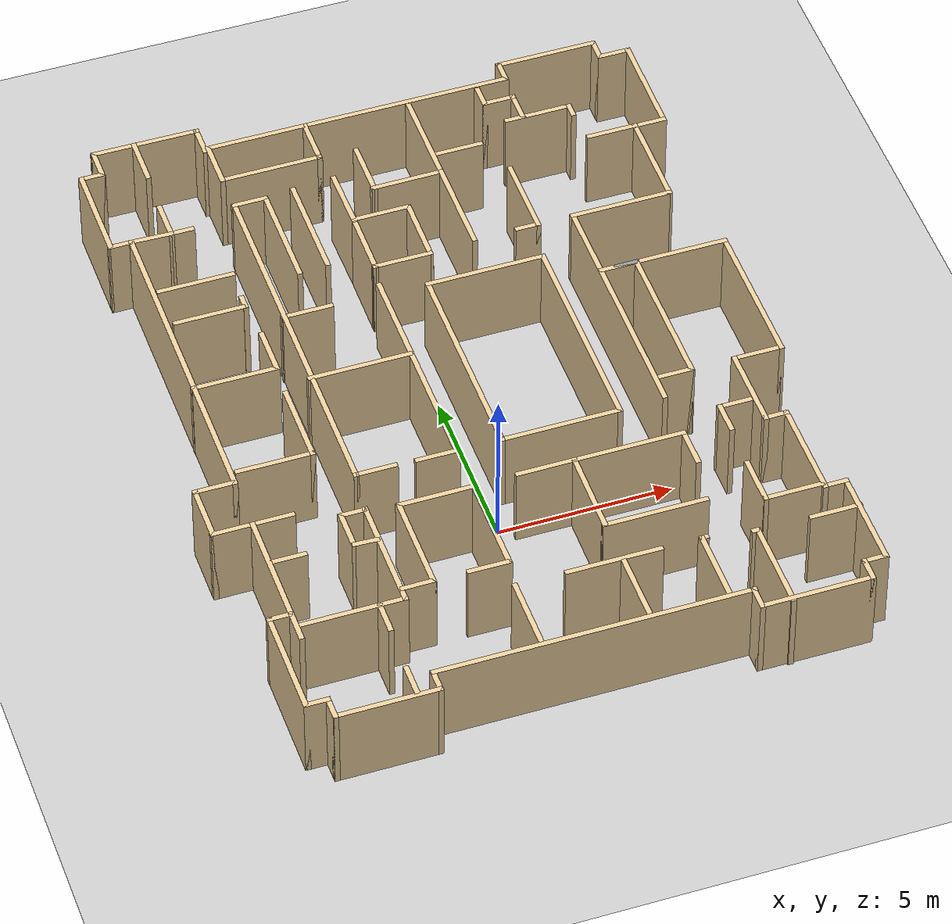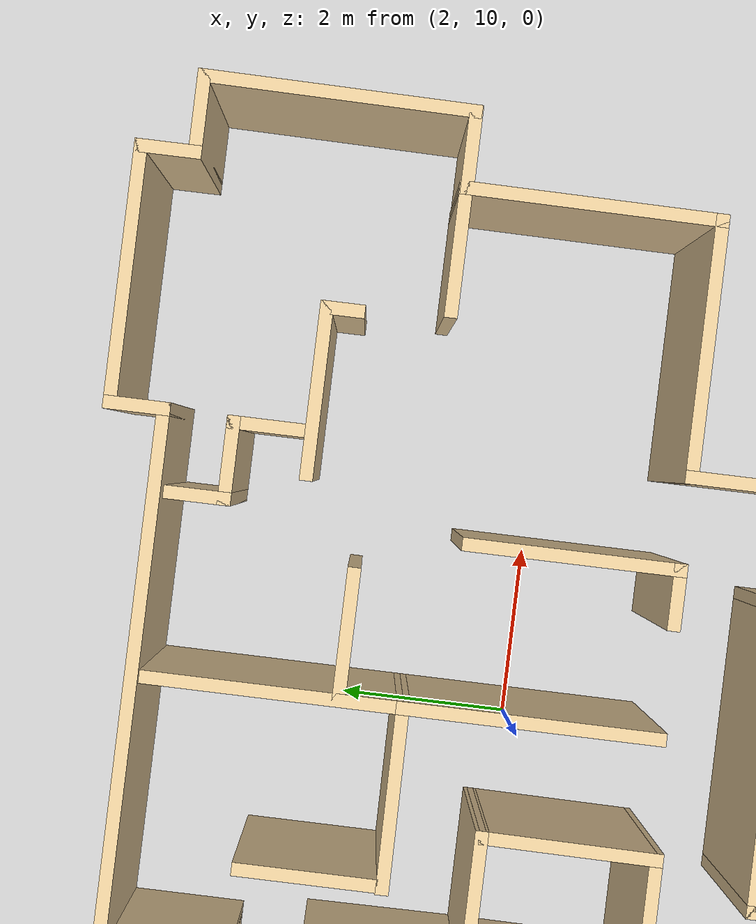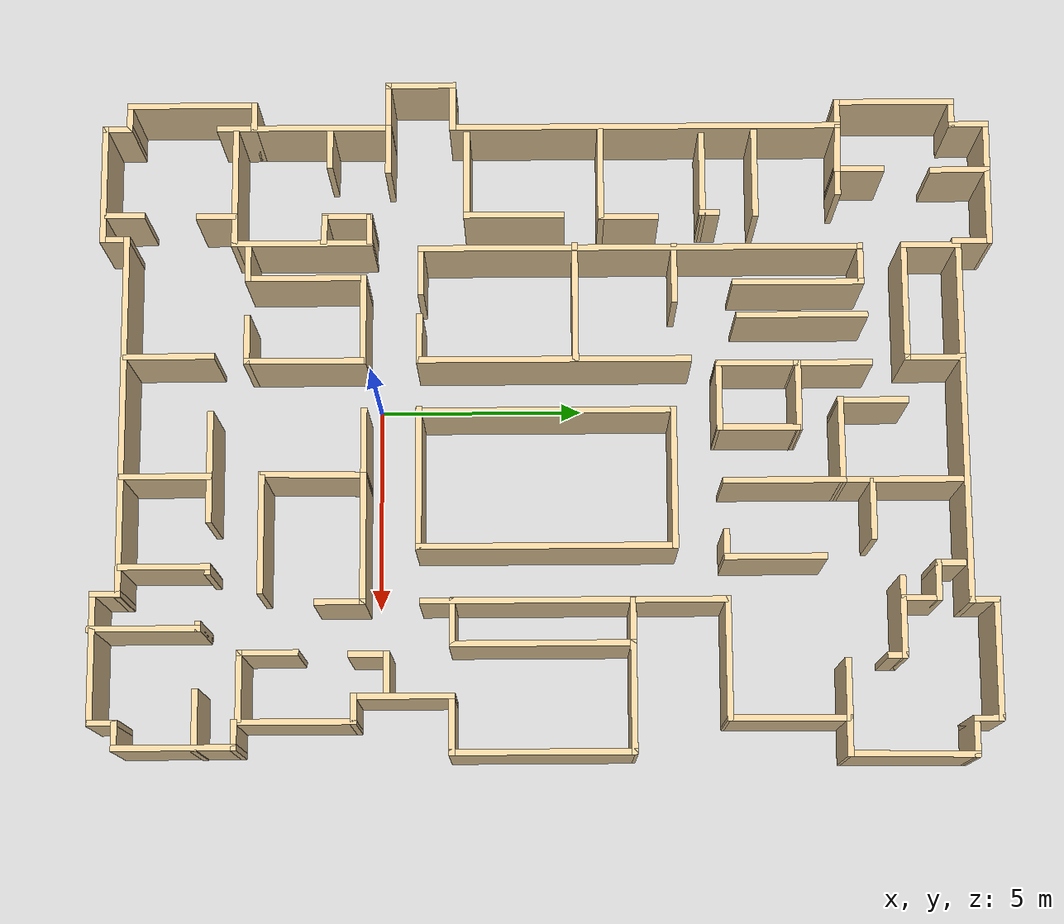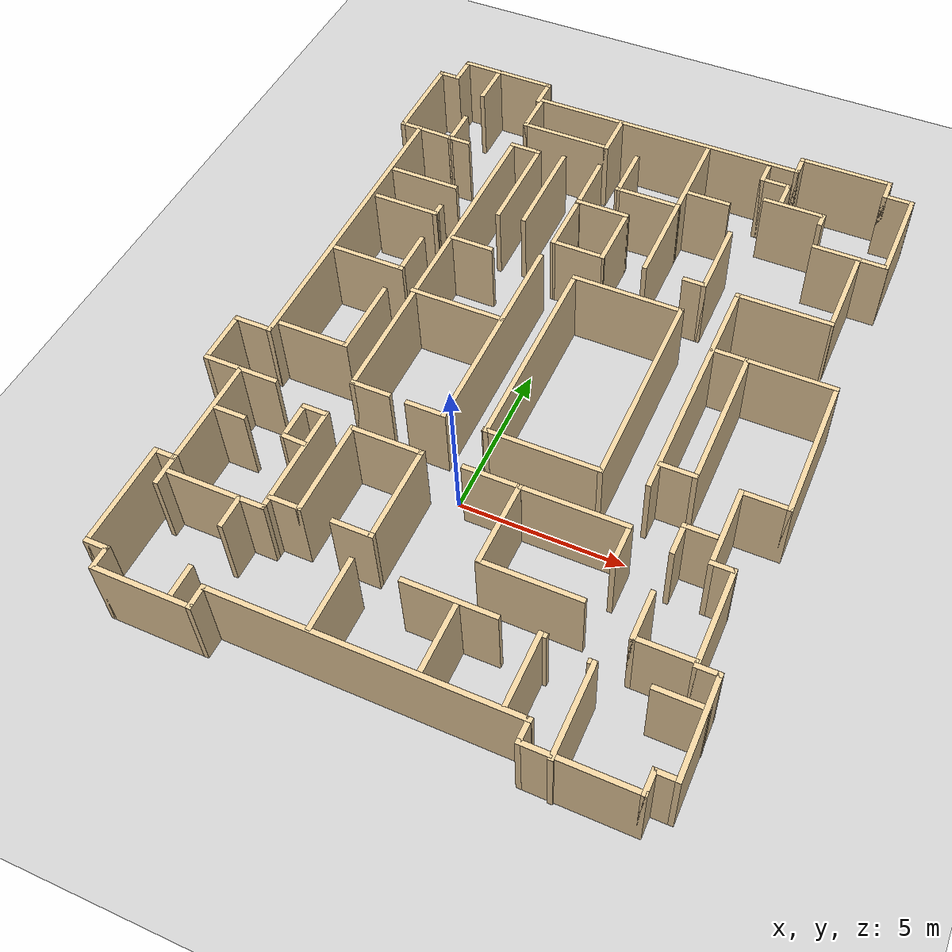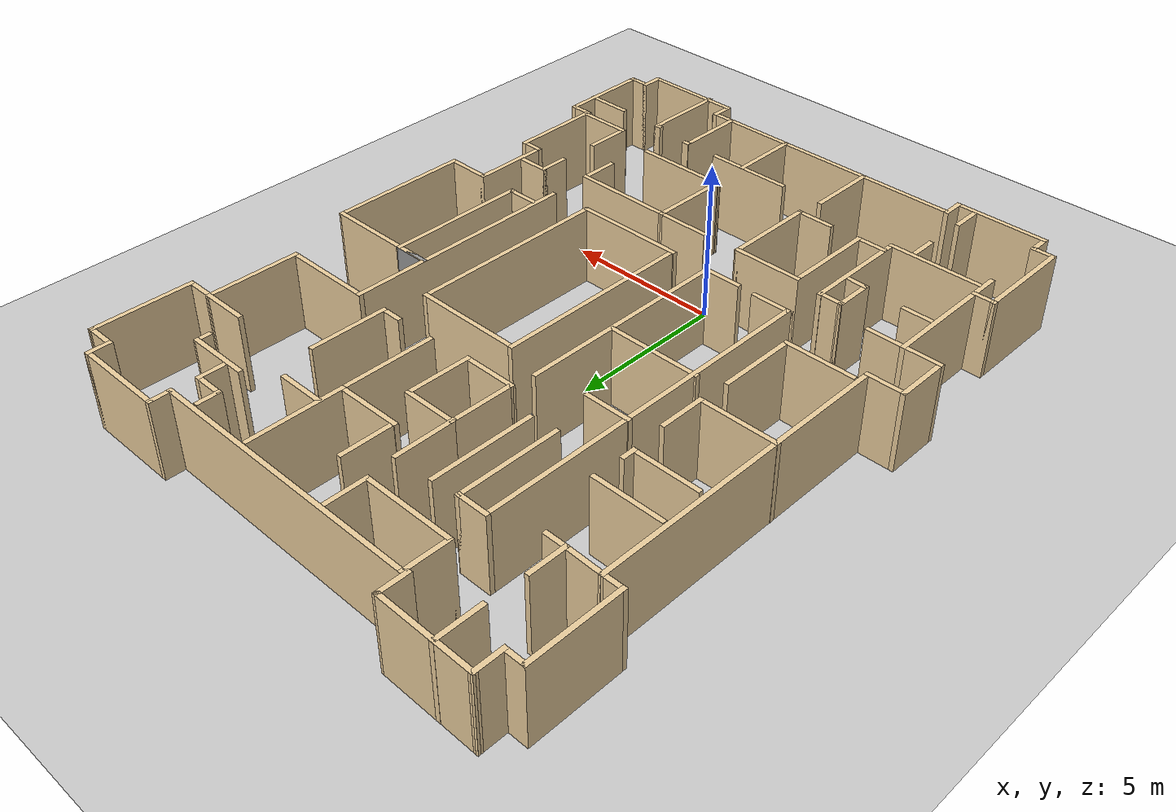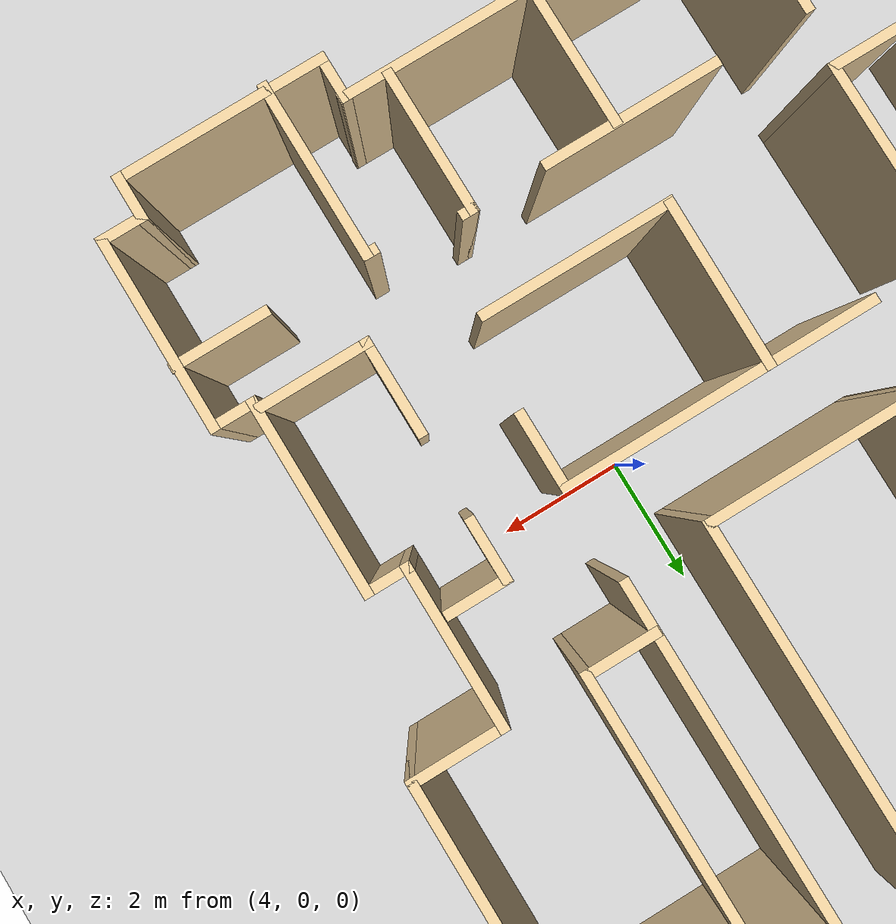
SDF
<sdf version="1.6">
 <world name="default">
  <light name="sun" type="directional">
   <pose>0 0 10 0 -0 0</pose>
   <diffuse>0.8 0.8 0.8 1</diffuse>
   <specular>0.1 0.1 0.1 1</specular>
   <attenuation>
    <range>1000</range>
    <constant>0.9</constant>
    <linear>0.01</linear>
    <quadratic>0.001</quadratic>
   </attenuation>
   <direction>-0.5 0.5 -1</direction>
  </light>
  <model name="ground_plane">
   <static>1</static>
   <link name="link">
    <collision name="collision">
     <geometry><plane><normal>0 0 1</normal><size>100 100</size></plane></geometry>
     <surface><friction><ode><mu>100</mu><mu2>50</mu2></ode></friction></surface>
    </collision>
    <visual name="visual">
     <cast_shadows>0</cast_shadows>
     <geometry><plane><normal>0 0 1</normal><size>100 100</size></plane></geometry>
     <material>
      <script><uri>file://media/materials/scripts/gazebo.material</uri><name>Gazebo/Grey</name></script>
     </material>
    </visual>
   </link>
  </model>
  <gravity>0 0 -9.8</gravity>
  <magnetic_field>6e-06 2.3e-05 -4.2e-05</magnetic_field>
  <atmosphere type="adiabatic"/>
  <physics name="default_physics" default="0" type="ode">
   <max_step_size>0.001</max_step_size>
   <real_time_factor>1</real_time_factor>
   <real_time_update_rate>1000</real_time_update_rate>
  </physics>
  <scene><ambient>0.4 0.4 0.4 1</ambient><background>0.7 0.7 0.7 1</background><shadows>1</shadows></scene>
  <spherical_coordinates>
   <surface_model>EARTH_WGS84</surface_model>
   <latitude_deg>0</latitude_deg>
   <longitude_deg>0</longitude_deg>
   <elevation>0</elevation>
   <heading_deg>0</heading_deg>
  </spherical_coordinates>
  <model name="ASTI_Floor_plan">
   <pose>0.499295 4.1368 0 0 -0 0</pose>
   <link name="Wall_0">
    <collision name="Wall_0_Collision">
     <geometry><box><size>3.5 0.15 2.5</size></box></geometry>
     <pose>0 0 1.25 0 -0 0</pose>
    </collision>
    <visual name="Wall_0_Visual">
     <pose>0 0 1.25 0 -0 0</pose>
     <geometry><box><size>3.5 0.15 2.5</size></box></geometry>
     <material>
      <script><uri>file://media/materials/scripts/gazebo.material</uri><name>Gazebo/Grey</name></script>
      <ambient>0.921569 0.807843 0.615686 1</ambient>
     </material>
    </visual>
    <pose>1.63239 3.09807 0 0 -0 0</pose>
   </link>
   <link name="Wall_1">
    <collision name="Wall_1_Collision">
     <geometry><box><size>6.36204 0.15 2.5</size></box></geometry>
     <pose>0 0 1.25 0 -0 0</pose>
    </collision>
    <visual name="Wall_1_Visual">
     <pose>0 0 1.25 0 -0 0</pose>
     <geometry><box><size>6.36204 0.15 2.5</size></box></geometry>
     <material>
      <script><uri>file://media/materials/scripts/gazebo.material</uri><name>Gazebo/Grey</name></script>
      <ambient>0.921569 0.807843 0.615686 1</ambient>
     </material>
    </visual>
    <pose>3.30739 -0.007754 0 0 0 -1.5708</pose>
   </link>
   <link name="Wall_100">
    <collision name="Wall_100_Collision">
     <geometry><box><size>9.75 0.15 2.5</size></box></geometry>
     <pose>0 0 1.25 0 -0 0</pose>
    </collision>
    <visual name="Wall_100_Visual">
     <pose>0 0 1.25 0 -0 0</pose>
     <geometry><box><size>9.75 0.15 2.5</size></box></geometry>
     <material>
      <script><uri>file://media/materials/scripts/gazebo.material</uri><name>Gazebo/Grey</name></script>
      <ambient>0.921569 0.807843 0.615686 1</ambient>
     </material>
    </visual>
    <pose>-7.28175 2.5015 0 0 -0 1.5708</pose>
   </link>
   <link name="Wall_101">
    <collision name="Wall_101_Collision">
     <geometry><box><size>0.75 0.15 2.5</size></box></geometry>
     <pose>0 0 1.25 0 -0 0</pose>
    </collision>
    <visual name="Wall_101_Visual">
     <pose>0 0 1.25 0 -0 0</pose>
     <geometry><box><size>0.75 0.15 2.5</size></box></geometry>
     <material>
      <script><uri>file://media/materials/scripts/gazebo.material</uri><name>Gazebo/Grey</name></script>
      <ambient>0.921569 0.807843 0.615686 1</ambient>
     </material>
    </visual>
    <pose>-7.58175 7.3015 0 0 -0 3.14159</pose>
   </link>
   <link name="Wall_102">
    <collision name="Wall_102_Collision">
     <geometry><box><size>3 0.15 2.5</size></box></geometry>
     <pose>0 0 1.25 0 -0 0</pose>
    </collision>
    <visual name="Wall_102_Visual">
     <pose>0 0 1.25 0 -0 0</pose>
     <geometry><box><size>3 0.15 2.5</size></box></geometry>
     <material>
      <script><uri>file://media/materials/scripts/gazebo.material</uri><name>Gazebo/Grey</name></script>
      <ambient>0.921569 0.807843 0.615686 1</ambient>
     </material>
    </visual>
    <pose>-7.88175 8.7265 0 0 -0 1.5708</pose>
   </link>
   <link name="Wall_103">
    <collision name="Wall_103_Collision">
     <geometry><box><size>0.75 0.15 2.5</size></box></geometry>
     <pose>0 0 1.25 0 -0 0</pose>
    </collision>
    <visual name="Wall_103_Visual">
     <pose>0 0 1.25 0 -0 0</pose>
     <geometry><box><size>0.75 0.15 2.5</size></box></geometry>
     <material>
      <script><uri>file://media/materials/scripts/gazebo.material</uri><name>Gazebo/Grey</name></script>
      <ambient>0.921569 0.807843 0.615686 1</ambient>
     </material>
    </visual>
    <pose>-7.58175 10.1515 0 0 -0 0</pose>
   </link>
   <link name="Wall_104">
    <collision name="Wall_104_Collision">
     <geometry><box><size>1 0.15 2.5</size></box></geometry>
     <pose>0 0 1.25 0 -0 0</pose>
    </collision>
    <visual name="Wall_104_Visual">
     <pose>0 0 1.25 0 -0 0</pose>
     <geometry><box><size>1 0.15 2.5</size></box></geometry>
     <material>
      <script><uri>file://media/materials/scripts/gazebo.material</uri><name>Gazebo/Grey</name></script>
      <ambient>0.921569 0.807843 0.615686 1</ambient>
     </material>
    </visual>
    <pose>-7.28175 10.5765 0 0 -0 1.5708</pose>
   </link>
   <link name="Wall_105">
    <collision name="Wall_105_Collision">
     <geometry><box><size>3.15536 0.15 2.5</size></box></geometry>
     <pose>0 0 1.25 0 -0 0</pose>
    </collision>
    <visual name="Wall_105_Visual">
     <pose>0 0 1.25 0 -0 0</pose>
     <geometry><box><size>3.15536 0.15 2.5</size></box></geometry>
     <material>
      <script><uri>file://media/materials/scripts/gazebo.material</uri><name>Gazebo/Grey</name></script>
      <ambient>0.921569 0.807843 0.615686 1</ambient>
     </material>
    </visual>
    <pose>-5.77911 10.9913 0 0 0 -0.006803</pose>
   </link>
   <link name="Wall_106">
    <collision name="Wall_106_Collision">
     <geometry><box><size>1 0.15 2.5</size></box></geometry>
     <pose>0 0 1.25 0 -0 0</pose>
    </collision>
    <visual name="Wall_106_Visual">
     <pose>0 0 1.25 0 -0 0</pose>
     <geometry><box><size>1 0.15 2.5</size></box></geometry>
     <material>
      <script><uri>file://media/materials/scripts/gazebo.material</uri><name>Gazebo/Grey</name></script>
      <ambient>0.921569 0.807843 0.615686 1</ambient>
     </material>
    </visual>
    <pose>-4.27646 10.5561 0 0 0 -1.5708</pose>
   </link>
   <link name="Wall_109">
    <collision name="Wall_109_Collision">
     <geometry><box><size>0.75 0.15 2.5</size></box></geometry>
     <pose>0 0 1.25 0 -0 0</pose>
    </collision>
    <visual name="Wall_109_Visual">
     <pose>0 0 1.25 0 -0 0</pose>
     <geometry><box><size>0.75 0.15 2.5</size></box></geometry>
     <material>
      <script><uri>file://media/materials/scripts/gazebo.material</uri><name>Gazebo/Grey</name></script>
      <ambient>0.921569 0.807843 0.615686 1</ambient>
     </material>
    </visual>
    <pose>4.68096 10.5034 0 0 -0 1.5708</pose>
   </link>
   <link name="Wall_11">
    <collision name="Wall_11_Collision">
     <geometry><box><size>3 0.15 2.5</size></box></geometry>
     <pose>0 0 1.25 0 -0 0</pose>
    </collision>
    <visual name="Wall_11_Visual">
     <pose>0 0 1.25 0 -0 0</pose>
     <geometry><box><size>3 0.15 2.5</size></box></geometry>
     <material>
      <script><uri>file://media/materials/scripts/gazebo.material</uri><name>Gazebo/Grey</name></script>
      <ambient>0.921569 0.807843 0.615686 1</ambient>
     </material>
    </visual>
    <pose>-2.78222 0.721913 0 0 -0 3.14159</pose>
   </link>
   <link name="Wall_110">
    <collision name="Wall_110_Collision">
     <geometry><box><size>3 0.15 2.5</size></box></geometry>
     <pose>0 0 1.25 0 -0 0</pose>
    </collision>
    <visual name="Wall_110_Visual">
     <pose>0 0 1.25 0 -0 0</pose>
     <geometry><box><size>3 0.15 2.5</size></box></geometry>
     <material>
      <script><uri>file://media/materials/scripts/gazebo.material</uri><name>Gazebo/Grey</name></script>
      <ambient>0.921569 0.807843 0.615686 1</ambient>
     </material>
    </visual>
    <pose>6.10596 10.8034 0 0 -0 0</pose>
   </link>
   <link name="Wall_111">
    <collision name="Wall_111_Collision">
     <geometry><box><size>0.75 0.15 2.5</size></box></geometry>
     <pose>0 0 1.25 0 -0 0</pose>
    </collision>
    <visual name="Wall_111_Visual">
     <pose>0 0 1.25 0 -0 0</pose>
     <geometry><box><size>0.75 0.15 2.5</size></box></geometry>
     <material>
      <script><uri>file://media/materials/scripts/gazebo.material</uri><name>Gazebo/Grey</name></script>
      <ambient>0.921569 0.807843 0.615686 1</ambient>
     </material>
    </visual>
    <pose>7.53096 10.5034 0 0 0 -1.5708</pose>
   </link>
   <link name="Wall_115">
    <collision name="Wall_115_Collision">
     <geometry><box><size>1 0.15 2.5</size></box></geometry>
     <pose>0 0 1.25 0 -0 0</pose>
    </collision>
    <visual name="Wall_115_Visual">
     <pose>0 0 1.25 0 -0 0</pose>
     <geometry><box><size>1 0.15 2.5</size></box></geometry>
     <material>
      <script><uri>file://media/materials/scripts/gazebo.material</uri><name>Gazebo/Grey</name></script>
      <ambient>0.921569 0.807843 0.615686 1</ambient>
     </material>
    </visual>
    <pose>7.92389 7.17644 0 0 -0 0</pose>
   </link>
   <link name="Wall_117">
    <collision name="Wall_117_Collision">
     <geometry><box><size>1 0.15 2.5</size></box></geometry>
     <pose>0 0 1.25 0 -0 0</pose>
    </collision>
    <visual name="Wall_117_Visual">
     <pose>0 0 1.25 0 -0 0</pose>
     <geometry><box><size>1 0.15 2.5</size></box></geometry>
     <material>
      <script><uri>file://media/materials/scripts/gazebo.material</uri><name>Gazebo/Grey</name></script>
      <ambient>0.921569 0.807843 0.615686 1</ambient>
     </material>
    </visual>
    <pose>7.95596 10.2034 0 0 -0 0</pose>
   </link>
   <link name="Wall_118">
    <collision name="Wall_118_Collision">
     <geometry><box><size>3.16721 0.15 2.5</size></box></geometry>
     <pose>0 0 1.25 0 -0 0</pose>
    </collision>
    <visual name="Wall_118_Visual">
     <pose>0 0 1.25 0 -0 0</pose>
     <geometry><box><size>3.16721 0.15 2.5</size></box></geometry>
     <material>
      <script><uri>file://media/materials/scripts/gazebo.material</uri><name>Gazebo/Grey</name></script>
      <ambient>0.921569 0.807843 0.615686 1</ambient>
     </material>
    </visual>
    <pose>8.36492 8.69485 0 0 0 -1.58143</pose>
   </link>
   <link name="Wall_120">
    <collision name="Wall_120_Collision">
     <geometry><box><size>3 0.15 2.5</size></box></geometry>
     <pose>0 0 1.25 0 -0 0</pose>
    </collision>
    <visual name="Wall_120_Visual">
     <pose>0 0 1.25 0 -0 0</pose>
     <geometry><box><size>3 0.15 2.5</size></box></geometry>
     <material>
      <script><uri>file://media/materials/scripts/gazebo.material</uri><name>Gazebo/Grey</name></script>
      <ambient>0.921569 0.807843 0.615686 1</ambient>
     </material>
    </visual>
    <pose>1.72424 5.76746 0 0 0 -1.5708</pose>
   </link>
   <link name="Wall_122">
    <collision name="Wall_122_Collision">
     <geometry><box><size>0.75 0.15 2.5</size></box></geometry>
     <pose>0 0 1.25 0 -0 0</pose>
    </collision>
    <visual name="Wall_122_Visual">
     <pose>0 0 1.25 0 -0 0</pose>
     <geometry><box><size>0.75 0.15 2.5</size></box></geometry>
     <material>
      <script><uri>file://media/materials/scripts/gazebo.material</uri><name>Gazebo/Grey</name></script>
      <ambient>0.921569 0.807843 0.615686 1</ambient>
     </material>
    </visual>
    <pose>3.29863 4.33598 0 0 -0 0</pose>
   </link>
   <link name="Wall_123">
    <collision name="Wall_123_Collision">
     <geometry><box><size>2.5 0.15 2.5</size></box></geometry>
     <pose>0 0 1.25 0 -0 0</pose>
    </collision>
    <visual name="Wall_123_Visual">
     <pose>0 0 1.25 0 -0 0</pose>
     <geometry><box><size>2.5 0.15 2.5</size></box></geometry>
     <material>
      <script><uri>file://media/materials/scripts/gazebo.material</uri><name>Gazebo/Grey</name></script>
      <ambient>0.921569 0.807843 0.615686 1</ambient>
     </material>
    </visual>
    <pose>3.59863 5.51098 0 0 -0 1.5708</pose>
   </link>
   <link name="Wall_126">
    <collision name="Wall_126_Collision">
     <geometry><box><size>1.25 0.15 2.5</size></box></geometry>
     <pose>0 0 1.25 0 -0 0</pose>
    </collision>
    <visual name="Wall_126_Visual">
     <pose>0 0 1.25 0 -0 0</pose>
     <geometry><box><size>1.25 0.15 2.5</size></box></geometry>
     <material>
      <script><uri>file://media/materials/scripts/gazebo.material</uri><name>Gazebo/Grey</name></script>
      <ambient>0.921569 0.807843 0.615686 1</ambient>
     </material>
    </visual>
    <pose>-6.73175 -3.8985 0 0 -0 0</pose>
   </link>
   <link name="Wall_129">
    <collision name="Wall_129_Collision">
     <geometry><box><size>1 0.15 2.5</size></box></geometry>
     <pose>0 0 1.25 0 -0 0</pose>
    </collision>
    <visual name="Wall_129_Visual">
     <pose>0 0 1.25 0 -0 0</pose>
     <geometry><box><size>1 0.15 2.5</size></box></geometry>
     <material>
      <script><uri>file://media/materials/scripts/gazebo.material</uri><name>Gazebo/Grey</name></script>
      <ambient>0.921569 0.807843 0.615686 1</ambient>
     </material>
    </visual>
    <pose>-6.73747 -5.34893 0 0 -0 3.14159</pose>
   </link>
   <link name="Wall_13">
    <collision name="Wall_13_Collision">
     <geometry><box><size>1.5 0.15 2.5</size></box></geometry>
     <pose>0 0 1.25 0 -0 0</pose>
    </collision>
    <visual name="Wall_13_Visual">
     <pose>0 0 1.25 0 -0 0</pose>
     <geometry><box><size>1.5 0.15 2.5</size></box></geometry>
     <material>
      <script><uri>file://media/materials/scripts/gazebo.material</uri><name>Gazebo/Grey</name></script>
      <ambient>0.921569 0.807843 0.615686 1</ambient>
     </material>
    </visual>
    <pose>-3.50184 3.16913 0 0 -0 0</pose>
   </link>
   <link name="Wall_132">
    <collision name="Wall_132_Collision">
     <geometry><box><size>1.25 0.15 2.5</size></box></geometry>
     <pose>0 0 1.25 0 -0 0</pose>
    </collision>
    <visual name="Wall_132_Visual">
     <pose>0 0 1.25 0 -0 0</pose>
     <geometry><box><size>1.25 0.15 2.5</size></box></geometry>
     <material>
      <script><uri>file://media/materials/scripts/gazebo.material</uri><name>Gazebo/Grey</name></script>
      <ambient>0.921569 0.807843 0.615686 1</ambient>
     </material>
    </visual>
    <pose>-4.97877 -4.90514 0 0 0 -1.5708</pose>
   </link>
   <link name="Wall_133">
    <collision name="Wall_133_Collision">
     <geometry><box><size>0.753676 0.15 2.5</size></box></geometry>
     <pose>0 0 1.25 0 -0 0</pose>
    </collision>
    <visual name="Wall_133_Visual">
     <pose>0 0 1.25 0 -0 0</pose>
     <geometry><box><size>0.753676 0.15 2.5</size></box></geometry>
     <material>
      <script><uri>file://media/materials/scripts/gazebo.material</uri><name>Gazebo/Grey</name></script>
      <ambient>0.921569 0.807843 0.615686 1</ambient>
     </material>
    </visual>
    <pose>-4.65106 -5.46822 0 0 0 -0.043335</pose>
   </link>
   <link name="Wall_136">
    <collision name="Wall_136_Collision">
     <geometry><box><size>0.75 0.15 2.5</size></box></geometry>
     <pose>0 0 1.25 0 -0 0</pose>
    </collision>
    <visual name="Wall_136_Visual">
     <pose>0 0 1.25 0 -0 0</pose>
     <geometry><box><size>0.75 0.15 2.5</size></box></geometry>
     <material>
      <script><uri>file://media/materials/scripts/gazebo.material</uri><name>Gazebo/Grey</name></script>
      <ambient>0.921569 0.807843 0.615686 1</ambient>
     </material>
    </visual>
    <pose>-4.65262 -4.35514 0 0 -0 0</pose>
   </link>
   <link name="Wall_138">
    <collision name="Wall_138_Collision">
     <geometry><box><size>3.5 0.15 2.5</size></box></geometry>
     <pose>0 0 1.25 0 -0 0</pose>
    </collision>
    <visual name="Wall_138_Visual">
     <pose>0 0 1.25 0 -0 0</pose>
     <geometry><box><size>3.5 0.15 2.5</size></box></geometry>
     <material>
      <script><uri>file://media/materials/scripts/gazebo.material</uri><name>Gazebo/Grey</name></script>
      <ambient>0.921569 0.807843 0.615686 1</ambient>
     </material>
    </visual>
    <pose>-4.29876 -6.01707 0 0 0 -1.5708</pose>
   </link>
   <link name="Wall_139">
    <collision name="Wall_139_Collision">
     <geometry><box><size>3 0.15 2.5</size></box></geometry>
     <pose>0 0 1.25 0 -0 0</pose>
    </collision>
    <visual name="Wall_139_Visual">
     <pose>0 0 1.25 0 -0 0</pose>
     <geometry><box><size>3 0.15 2.5</size></box></geometry>
     <material>
      <script><uri>file://media/materials/scripts/gazebo.material</uri><name>Gazebo/Grey</name></script>
      <ambient>0.921569 0.807843 0.615686 1</ambient>
     </material>
    </visual>
    <pose>-5.72376 -7.69207 0 0 -0 3.14159</pose>
   </link>
   <link name="Wall_141">
    <collision name="Wall_141_Collision">
     <geometry><box><size>1 0.15 2.5</size></box></geometry>
     <pose>0 0 1.25 0 -0 0</pose>
    </collision>
    <visual name="Wall_141_Visual">
     <pose>0 0 1.25 0 -0 0</pose>
     <geometry><box><size>1 0.15 2.5</size></box></geometry>
     <material>
      <script><uri>file://media/materials/scripts/gazebo.material</uri><name>Gazebo/Grey</name></script>
      <ambient>0.921569 0.807843 0.615686 1</ambient>
     </material>
    </visual>
    <pose>-7.28175 -7.6735 0 0 0 -1.5708</pose>
   </link>
   <link name="Wall_143">
    <collision name="Wall_143_Collision">
     <geometry><box><size>1 0.15 2.5</size></box></geometry>
     <pose>0 0 1.25 0 -0 0</pose>
    </collision>
    <visual name="Wall_143_Visual">
     <pose>0 0 1.25 0 -0 0</pose>
     <geometry><box><size>1 0.15 2.5</size></box></geometry>
     <material>
      <script><uri>file://media/materials/scripts/gazebo.material</uri><name>Gazebo/Grey</name></script>
      <ambient>0.921569 0.807843 0.615686 1</ambient>
     </material>
    </visual>
    <pose>-3.83544 -7.34075 0 0 -0 0</pose>
   </link>
   <link name="Wall_144">
    <collision name="Wall_144_Collision">
     <geometry><box><size>3 0.15 2.5</size></box></geometry>
     <pose>0 0 1.25 0 -0 0</pose>
    </collision>
    <visual name="Wall_144_Visual">
     <pose>0 0 1.25 0 -0 0</pose>
     <geometry><box><size>3 0.15 2.5</size></box></geometry>
     <material>
      <script><uri>file://media/materials/scripts/gazebo.material</uri><name>Gazebo/Grey</name></script>
      <ambient>0.921569 0.807843 0.615686 1</ambient>
     </material>
    </visual>
    <pose>-3.41044 -5.91575 0 0 -0 1.5708</pose>
   </link>
   <link name="Wall_145">
    <collision name="Wall_145_Collision">
     <geometry><box><size>2.25 0.15 2.5</size></box></geometry>
     <pose>0 0 1.25 0 -0 0</pose>
    </collision>
    <visual name="Wall_145_Visual">
     <pose>0 0 1.25 0 -0 0</pose>
     <geometry><box><size>2.25 0.15 2.5</size></box></geometry>
     <material>
      <script><uri>file://media/materials/scripts/gazebo.material</uri><name>Gazebo/Grey</name></script>
      <ambient>0.921569 0.807843 0.615686 1</ambient>
     </material>
    </visual>
    <pose>-2.36044 -4.49075 0 0 -0 0</pose>
   </link>
   <link name="Wall_146">
    <collision name="Wall_146_Collision">
     <geometry><box><size>3 0.15 2.5</size></box></geometry>
     <pose>0 0 1.25 0 -0 0</pose>
    </collision>
    <visual name="Wall_146_Visual">
     <pose>0 0 1.25 0 -0 0</pose>
     <geometry><box><size>3 0.15 2.5</size></box></geometry>
     <material>
      <script><uri>file://media/materials/scripts/gazebo.material</uri><name>Gazebo/Grey</name></script>
      <ambient>0.921569 0.807843 0.615686 1</ambient>
     </material>
    </visual>
    <pose>-1.31044 -5.91575 0 0 0 -1.5708</pose>
   </link>
   <link name="Wall_147">
    <collision name="Wall_147_Collision">
     <geometry><box><size>1.25 0.15 2.5</size></box></geometry>
     <pose>0 0 1.25 0 -0 0</pose>
    </collision>
    <visual name="Wall_147_Visual">
     <pose>0 0 1.25 0 -0 0</pose>
     <geometry><box><size>1.25 0.15 2.5</size></box></geometry>
     <material>
      <script><uri>file://media/materials/scripts/gazebo.material</uri><name>Gazebo/Grey</name></script>
      <ambient>0.921569 0.807843 0.615686 1</ambient>
     </material>
    </visual>
    <pose>-1.86044 -7.34075 0 0 -0 3.14159</pose>
   </link>
   <link name="Wall_149">
    <collision name="Wall_149_Collision">
     <geometry><box><size>1.75 0.15 2.5</size></box></geometry>
     <pose>0 0 1.25 0 -0 0</pose>
    </collision>
    <visual name="Wall_149_Visual">
     <pose>0 0 1.25 0 -0 0</pose>
     <geometry><box><size>1.75 0.15 2.5</size></box></geometry>
     <material>
      <script><uri>file://media/materials/scripts/gazebo.material</uri><name>Gazebo/Grey</name></script>
      <ambient>0.921569 0.807843 0.615686 1</ambient>
     </material>
    </visual>
    <pose>0.740282 -4.4528 0 0 -0 0</pose>
   </link>
   <link name="Wall_15">
    <collision name="Wall_15_Collision">
     <geometry><box><size>1.04066 0.15 2.5</size></box></geometry>
     <pose>0 0 1.25 0 -0 0</pose>
    </collision>
    <visual name="Wall_15_Visual">
     <pose>0 0 1.25 0 -0 0</pose>
     <geometry><box><size>1.04066 0.15 2.5</size></box></geometry>
     <material>
      <script><uri>file://media/materials/scripts/gazebo.material</uri><name>Gazebo/Grey</name></script>
      <ambient>0.921569 0.807843 0.615686 1</ambient>
     </material>
    </visual>
    <pose>-3.70491 7.77097 0 0 -0 0</pose>
   </link>
   <link name="Wall_150">
    <collision name="Wall_150_Collision">
     <geometry><box><size>2.59634 0.15 2.5</size></box></geometry>
     <pose>0 0 1.25 0 -0 0</pose>
    </collision>
    <visual name="Wall_150_Visual">
     <pose>0 0 1.25 0 -0 0</pose>
     <geometry><box><size>2.59634 0.15 2.5</size></box></geometry>
     <material>
      <script><uri>file://media/materials/scripts/gazebo.material</uri><name>Gazebo/Grey</name></script>
      <ambient>0.921569 0.807843 0.615686 1</ambient>
     </material>
    </visual>
    <pose>1.52721 -5.6759 0 0 0 -1.58149</pose>
   </link>
   <link name="Wall_152">
    <collision name="Wall_152_Collision">
     <geometry><box><size>3.25 0.15 2.5</size></box></geometry>
     <pose>0 0 1.25 0 -0 0</pose>
    </collision>
    <visual name="Wall_152_Visual">
     <pose>0 0 1.25 0 -0 0</pose>
     <geometry><box><size>3.25 0.15 2.5</size></box></geometry>
     <material>
      <script><uri>file://media/materials/scripts/gazebo.material</uri><name>Gazebo/Grey</name></script>
      <ambient>0.921569 0.807843 0.615686 1</ambient>
     </material>
    </visual>
    <pose>3.09028 -4.4528 0 0 -0 0</pose>
   </link>
   <link name="Wall_153">
    <collision name="Wall_153_Collision">
     <geometry><box><size>1.25 0.15 2.5</size></box></geometry>
     <pose>0 0 1.25 0 -0 0</pose>
    </collision>
    <visual name="Wall_153_Visual">
     <pose>0 0 1.25 0 -0 0</pose>
     <geometry><box><size>1.25 0.15 2.5</size></box></geometry>
     <material>
      <script><uri>file://media/materials/scripts/gazebo.material</uri><name>Gazebo/Grey</name></script>
      <ambient>0.921569 0.807843 0.615686 1</ambient>
     </material>
    </visual>
    <pose>4.64028 -5.00281 0 0 0 -1.5708</pose>
   </link>
   <link name="Wall_155">
    <collision name="Wall_155_Collision">
     <geometry><box><size>3 0.15 2.5</size></box></geometry>
     <pose>0 0 1.25 0 -0 0</pose>
    </collision>
    <visual name="Wall_155_Visual">
     <pose>0 0 1.25 0 -0 0</pose>
     <geometry><box><size>3 0.15 2.5</size></box></geometry>
     <material>
      <script><uri>file://media/materials/scripts/gazebo.material</uri><name>Gazebo/Grey</name></script>
      <ambient>0.921569 0.807843 0.615686 1</ambient>
     </material>
    </visual>
    <pose>2.93913 -6.92515 0 0 -0 3.14159</pose>
   </link>
   <link name="Wall_157">
    <collision name="Wall_157_Collision">
     <geometry><box><size>1 0.15 2.5</size></box></geometry>
     <pose>0 0 1.25 0 -0 0</pose>
    </collision>
    <visual name="Wall_157_Visual">
     <pose>0 0 1.25 0 -0 0</pose>
     <geometry><box><size>1 0.15 2.5</size></box></geometry>
     <material>
      <script><uri>file://media/materials/scripts/gazebo.material</uri><name>Gazebo/Grey</name></script>
      <ambient>0.921569 0.807843 0.615686 1</ambient>
     </material>
    </visual>
    <pose>-5.00425 -8.15258 0 0 0 -1.5708</pose>
   </link>
   <link name="Wall_159">
    <collision name="Wall_159_Collision">
     <geometry><box><size>1 0.15 2.5</size></box></geometry>
     <pose>0 0 1.25 0 -0 0</pose>
    </collision>
    <visual name="Wall_159_Visual">
     <pose>0 0 1.25 0 -0 0</pose>
     <geometry><box><size>1 0.15 2.5</size></box></geometry>
     <material>
      <script><uri>file://media/materials/scripts/gazebo.material</uri><name>Gazebo/Grey</name></script>
      <ambient>0.921569 0.807843 0.615686 1</ambient>
     </material>
    </visual>
    <pose>-5.03883 -10.4165 0 0 0 -1.5708</pose>
   </link>
   <link name="Wall_16">
    <collision name="Wall_16_Collision">
     <geometry><box><size>3.25 0.15 2.5</size></box></geometry>
     <pose>0 0 1.25 0 -0 0</pose>
    </collision>
    <visual name="Wall_16_Visual">
     <pose>0 0 1.25 0 -0 0</pose>
     <geometry><box><size>3.25 0.15 2.5</size></box></geometry>
     <material>
      <script><uri>file://media/materials/scripts/gazebo.material</uri><name>Gazebo/Grey</name></script>
      <ambient>0.921569 0.807843 0.615686 1</ambient>
     </material>
    </visual>
    <pose>-3.24463 6.22097 0 0 0 -1.5708</pose>
   </link>
   <link name="Wall_161">
    <collision name="Wall_161_Collision">
     <geometry><box><size>2.25 0.15 2.5</size></box></geometry>
     <pose>0 0 1.25 0 -0 0</pose>
    </collision>
    <visual name="Wall_161_Visual">
     <pose>0 0 1.25 0 -0 0</pose>
     <geometry><box><size>2.25 0.15 2.5</size></box></geometry>
     <material>
      <script><uri>file://media/materials/scripts/gazebo.material</uri><name>Gazebo/Grey</name></script>
      <ambient>0.921569 0.807843 0.615686 1</ambient>
     </material>
    </visual>
    <pose>-1.44187 -9.24449 0 0 0 -1.5708</pose>
   </link>
   <link name="Wall_163">
    <collision name="Wall_163_Collision">
     <geometry><box><size>2.75 0.15 2.5</size></box></geometry>
     <pose>0 0 1.25 0 -0 0</pose>
    </collision>
    <visual name="Wall_163_Visual">
     <pose>0 0 1.25 0 -0 0</pose>
     <geometry><box><size>2.75 0.15 2.5</size></box></geometry>
     <material>
      <script><uri>file://media/materials/scripts/gazebo.material</uri><name>Gazebo/Grey</name></script>
      <ambient>0.921569 0.807843 0.615686 1</ambient>
     </material>
    </visual>
    <pose>1.30974 -8.19449 0 0 -0 0</pose>
   </link>
   <link name="Wall_165">
    <collision name="Wall_165_Collision">
     <geometry><box><size>2.25 0.15 2.5</size></box></geometry>
     <pose>0 0 1.25 0 -0 0</pose>
    </collision>
    <visual name="Wall_165_Visual">
     <pose>0 0 1.25 0 -0 0</pose>
     <geometry><box><size>2.25 0.15 2.5</size></box></geometry>
     <material>
      <script><uri>file://media/materials/scripts/gazebo.material</uri><name>Gazebo/Grey</name></script>
      <ambient>0.921569 0.807843 0.615686 1</ambient>
     </material>
    </visual>
    <pose>1.54984 -9.26178 0 0 0 -1.5708</pose>
   </link>
   <link name="Wall_167">
    <collision name="Wall_167_Collision">
     <geometry><box><size>0.25 0.15 2.5</size></box></geometry>
     <pose>0 0 1.25 0 -0 0</pose>
    </collision>
    <visual name="Wall_167_Visual">
     <pose>0 0 1.25 0 -0 0</pose>
     <geometry><box><size>0.25 0.15 2.5</size></box></geometry>
     <material>
      <script><uri>file://media/materials/scripts/gazebo.material</uri><name>Gazebo/Grey</name></script>
      <ambient>0.921569 0.807843 0.615686 1</ambient>
     </material>
    </visual>
    <pose>3.83441 -8.19449 0 0 -0 3.14159</pose>
   </link>
   <link name="Wall_168">
    <collision name="Wall_168_Collision">
     <geometry><box><size>2.25 0.15 2.5</size></box></geometry>
     <pose>0 0 1.25 0 -0 0</pose>
    </collision>
    <visual name="Wall_168_Visual">
     <pose>0 0 1.25 0 -0 0</pose>
     <geometry><box><size>2.25 0.15 2.5</size></box></geometry>
     <material>
      <script><uri>file://media/materials/scripts/gazebo.material</uri><name>Gazebo/Grey</name></script>
      <ambient>0.921569 0.807843 0.615686 1</ambient>
     </material>
    </visual>
    <pose>3.76712 -9.24449 0 0 0 -1.5708</pose>
   </link>
   <link name="Wall_170">
    <collision name="Wall_170_Collision">
     <geometry><box><size>0.25 0.15 2.5</size></box></geometry>
     <pose>0 0 1.25 0 -0 0</pose>
    </collision>
    <visual name="Wall_170_Visual">
     <pose>0 0 1.25 0 -0 0</pose>
     <geometry><box><size>0.25 0.15 2.5</size></box></geometry>
     <material>
      <script><uri>file://media/materials/scripts/gazebo.material</uri><name>Gazebo/Grey</name></script>
      <ambient>0.921569 0.807843 0.615686 1</ambient>
     </material>
    </visual>
    <pose>5.2141 -8.40201 0 0 -0 0</pose>
   </link>
   <link name="Wall_171">
    <collision name="Wall_171_Collision">
     <geometry><box><size>2.75 0.15 2.5</size></box></geometry>
     <pose>0 0 1.25 0 -0 0</pose>
    </collision>
    <visual name="Wall_171_Visual">
     <pose>0 0 1.25 0 -0 0</pose>
     <geometry><box><size>2.75 0.15 2.5</size></box></geometry>
     <material>
      <script><uri>file://media/materials/scripts/gazebo.material</uri><name>Gazebo/Grey</name></script>
      <ambient>0.921569 0.807843 0.615686 1</ambient>
     </material>
    </visual>
    <pose>5.2641 -9.70201 0 0 0 -1.5708</pose>
   </link>
   <link name="Wall_173">
    <collision name="Wall_173_Collision">
     <geometry><box><size>1.5 0.15 2.5</size></box></geometry>
     <pose>0 0 1.25 0 -0 0</pose>
    </collision>
    <visual name="Wall_173_Visual">
     <pose>0 0 1.25 0 -0 0</pose>
     <geometry><box><size>1.5 0.15 2.5</size></box></geometry>
     <material>
      <script><uri>file://media/materials/scripts/gazebo.material</uri><name>Gazebo/Grey</name></script>
      <ambient>0.921569 0.807843 0.615686 1</ambient>
     </material>
    </visual>
    <pose>7.46315 -8.43659 0 0 -0 0</pose>
   </link>
   <link name="Wall_175">
    <collision name="Wall_175_Collision">
     <geometry><box><size>1 0.15 2.5</size></box></geometry>
     <pose>0 0 1.25 0 -0 0</pose>
    </collision>
    <visual name="Wall_175_Visual">
     <pose>0 0 1.25 0 -0 0</pose>
     <geometry><box><size>1 0.15 2.5</size></box></geometry>
     <material>
      <script><uri>file://media/materials/scripts/gazebo.material</uri><name>Gazebo/Grey</name></script>
      <ambient>0.921569 0.807843 0.615686 1</ambient>
     </material>
    </visual>
    <pose>6.33251 -3.8679 0 0 -0 3.14159</pose>
   </link>
   <link name="Wall_176">
    <collision name="Wall_176_Collision">
     <geometry><box><size>1 0.15 2.5</size></box></geometry>
     <pose>0 0 1.25 0 -0 0</pose>
    </collision>
    <visual name="Wall_176_Visual">
     <pose>0 0 1.25 0 -0 0</pose>
     <geometry><box><size>1 0.15 2.5</size></box></geometry>
     <material>
      <script><uri>file://media/materials/scripts/gazebo.material</uri><name>Gazebo/Grey</name></script>
      <ambient>0.921569 0.807843 0.615686 1</ambient>
     </material>
    </visual>
    <pose>5.90751 -4.2929 0 0 0 -1.5708</pose>
   </link>
   <link name="Wall_178">
    <collision name="Wall_178_Collision">
     <geometry><box><size>1.5 0.15 2.5</size></box></geometry>
     <pose>0 0 1.25 0 -0 0</pose>
    </collision>
    <visual name="Wall_178_Visual">
     <pose>0 0 1.25 0 -0 0</pose>
     <geometry><box><size>1.5 0.15 2.5</size></box></geometry>
     <material>
      <script><uri>file://media/materials/scripts/gazebo.material</uri><name>Gazebo/Grey</name></script>
      <ambient>0.921569 0.807843 0.615686 1</ambient>
     </material>
    </visual>
    <pose>5.86259 -6.72477 0 0 0 -1.5708</pose>
   </link>
   <link name="Wall_179">
    <collision name="Wall_179_Collision">
     <geometry><box><size>1.75 0.15 2.5</size></box></geometry>
     <pose>0 0 1.25 0 -0 0</pose>
    </collision>
    <visual name="Wall_179_Visual">
     <pose>0 0 1.25 0 -0 0</pose>
     <geometry><box><size>1.75 0.15 2.5</size></box></geometry>
     <material>
      <script><uri>file://media/materials/scripts/gazebo.material</uri><name>Gazebo/Grey</name></script>
      <ambient>0.921569 0.807843 0.615686 1</ambient>
     </material>
    </visual>
    <pose>6.66259 -7.39977 0 0 -0 0</pose>
   </link>
   <link name="Wall_18">
    <collision name="Wall_18_Collision">
     <geometry><box><size>3.25 0.15 2.5</size></box></geometry>
     <pose>0 0 1.25 0 -0 0</pose>
    </collision>
    <visual name="Wall_18_Visual">
     <pose>0 0 1.25 0 -0 0</pose>
     <geometry><box><size>3.25 0.15 2.5</size></box></geometry>
     <material>
      <script><uri>file://media/materials/scripts/gazebo.material</uri><name>Gazebo/Grey</name></script>
      <ambient>0.921569 0.807843 0.615686 1</ambient>
     </material>
    </visual>
    <pose>-2.41289 6.29416 0 0 0 -1.5708</pose>
   </link>
   <link name="Wall_181">
    <collision name="Wall_181_Collision">
     <geometry><box><size>1.5 0.15 2.5</size></box></geometry>
     <pose>0 0 1.25 0 -0 0</pose>
    </collision>
    <visual name="Wall_181_Visual">
     <pose>0 0 1.25 0 -0 0</pose>
     <geometry><box><size>1.5 0.15 2.5</size></box></geometry>
     <material>
      <script><uri>file://media/materials/scripts/gazebo.material</uri><name>Gazebo/Grey</name></script>
      <ambient>0.921569 0.807843 0.615686 1</ambient>
     </material>
    </visual>
    <pose>-4.93985 2.0518 0 0 0 -1.5708</pose>
   </link>
   <link name="Wall_184">
    <collision name="Wall_184_Collision">
     <geometry><box><size>1.5 0.15 2.5</size></box></geometry>
     <pose>0 0 1.25 0 -0 0</pose>
    </collision>
    <visual name="Wall_184_Visual">
     <pose>0 0 1.25 0 -0 0</pose>
     <geometry><box><size>1.5 0.15 2.5</size></box></geometry>
     <material>
      <script><uri>file://media/materials/scripts/gazebo.material</uri><name>Gazebo/Grey</name></script>
      <ambient>0.921569 0.807843 0.615686 1</ambient>
     </material>
    </visual>
    <pose>-6.09951 10.3225 0 0 0 -1.5708</pose>
   </link>
   <link name="Wall_186">
    <collision name="Wall_186_Collision">
     <geometry><box><size>1.25 0.15 2.5</size></box></geometry>
     <pose>0 0 1.25 0 -0 0</pose>
    </collision>
    <visual name="Wall_186_Visual">
     <pose>0 0 1.25 0 -0 0</pose>
     <geometry><box><size>1.25 0.15 2.5</size></box></geometry>
     <material>
      <script><uri>file://media/materials/scripts/gazebo.material</uri><name>Gazebo/Grey</name></script>
      <ambient>0.921569 0.807843 0.615686 1</ambient>
     </material>
    </visual>
    <pose>-6.14437 7.81586 0 0 0 -1.5708</pose>
   </link>
   <link name="Wall_187">
    <collision name="Wall_187_Collision">
     <geometry><box><size>1.28794 0.15 2.5</size></box></geometry>
     <pose>0 0 1.25 0 -0 0</pose>
    </collision>
    <visual name="Wall_187_Visual">
     <pose>0 0 1.25 0 -0 0</pose>
     <geometry><box><size>1.28794 0.15 2.5</size></box></geometry>
     <material>
      <script><uri>file://media/materials/scripts/gazebo.material</uri><name>Gazebo/Grey</name></script>
      <ambient>0.921569 0.807843 0.615686 1</ambient>
     </material>
    </visual>
    <pose>-6.71306 7.28368 0 0 -0 3.11027</pose>
   </link>
   <link name="Wall_189">
    <collision name="Wall_189_Collision">
     <geometry><box><size>0.75 0.15 2.5</size></box></geometry>
     <pose>0 0 1.25 0 -0 0</pose>
    </collision>
    <visual name="Wall_189_Visual">
     <pose>0 0 1.25 0 -0 0</pose>
     <geometry><box><size>0.75 0.15 2.5</size></box></geometry>
     <material>
      <script><uri>file://media/materials/scripts/gazebo.material</uri><name>Gazebo/Grey</name></script>
      <ambient>0.921569 0.807843 0.615686 1</ambient>
     </material>
    </visual>
    <pose>-5.84437 7.26586 0 0 -0 0</pose>
   </link>
   <link name="Wall_2">
    <collision name="Wall_2_Collision">
     <geometry><box><size>3.5 0.15 2.5</size></box></geometry>
     <pose>0 0 1.25 0 -0 0</pose>
    </collision>
    <visual name="Wall_2_Visual">
     <pose>0 0 1.25 0 -0 0</pose>
     <geometry><box><size>3.5 0.15 2.5</size></box></geometry>
     <material>
      <script><uri>file://media/materials/scripts/gazebo.material</uri><name>Gazebo/Grey</name></script>
      <ambient>0.921569 0.807843 0.615686 1</ambient>
     </material>
    </visual>
    <pose>1.5978 -3.11358 0 0 -0 3.14159</pose>
   </link>
   <link name="Wall_25">
    <collision name="Wall_25_Collision">
     <geometry><box><size>1.95283 0.15 2.5</size></box></geometry>
     <pose>0 0 1.25 0 -0 0</pose>
    </collision>
    <visual name="Wall_25_Visual">
     <pose>0 0 1.25 0 -0 0</pose>
     <geometry><box><size>1.95283 0.15 2.5</size></box></geometry>
     <material>
      <script><uri>file://media/materials/scripts/gazebo.material</uri><name>Gazebo/Grey</name></script>
      <ambient>0.921569 0.807843 0.615686 1</ambient>
     </material>
    </visual>
    <pose>-1.19089 7.01799 0 0 0 -1.5625</pose>
   </link>
   <link name="Wall_28">
    <collision name="Wall_28_Collision">
     <geometry><box><size>2.04729 0.15 2.5</size></box></geometry>
     <pose>0 0 1.25 0 -0 0</pose>
    </collision>
    <visual name="Wall_28_Visual">
     <pose>0 0 1.25 0 -0 0</pose>
     <geometry><box><size>2.04729 0.15 2.5</size></box></geometry>
     <material>
      <script><uri>file://media/materials/scripts/gazebo.material</uri><name>Gazebo/Grey</name></script>
      <ambient>0.921569 0.807843 0.615686 1</ambient>
     </material>
    </visual>
    <pose>-1.19089 5.168 0 0 0 -1.57868</pose>
   </link>
   <link name="Wall_29">
    <collision name="Wall_29_Collision">
     <geometry><box><size>1.75 0.15 2.5</size></box></geometry>
     <pose>0 0 1.25 0 -0 0</pose>
    </collision>
    <visual name="Wall_29_Visual">
     <pose>0 0 1.25 0 -0 0</pose>
     <geometry><box><size>1.75 0.15 2.5</size></box></geometry>
     <material>
      <script><uri>file://media/materials/scripts/gazebo.material</uri><name>Gazebo/Grey</name></script>
      <ambient>0.921569 0.807843 0.615686 1</ambient>
     </material>
    </visual>
    <pose>-0.398371 4.21938 0 0 -0 0</pose>
   </link>
   <link name="Wall_3">
    <collision name="Wall_3_Collision">
     <geometry><box><size>6.36204 0.15 2.5</size></box></geometry>
     <pose>0 0 1.25 0 -0 0</pose>
    </collision>
    <visual name="Wall_3_Visual">
     <pose>0 0 1.25 0 -0 0</pose>
     <geometry><box><size>6.36204 0.15 2.5</size></box></geometry>
     <material>
      <script><uri>file://media/materials/scripts/gazebo.material</uri><name>Gazebo/Grey</name></script>
      <ambient>0.921569 0.807843 0.615686 1</ambient>
     </material>
    </visual>
    <pose>-0.04261 -0.007754 0 0 -0 1.5708</pose>
   </link>
   <link name="Wall_30">
    <collision name="Wall_30_Collision">
     <geometry><box><size>2.04729 0.15 2.5</size></box></geometry>
     <pose>0 0 1.25 0 -0 0</pose>
    </collision>
    <visual name="Wall_30_Visual">
     <pose>0 0 1.25 0 -0 0</pose>
     <geometry><box><size>2.04729 0.15 2.5</size></box></geometry>
     <material>
      <script><uri>file://media/materials/scripts/gazebo.material</uri><name>Gazebo/Grey</name></script>
      <ambient>0.921569 0.807843 0.615686 1</ambient>
     </material>
    </visual>
    <pose>0.409106 5.168 0 0 -0 1.56292</pose>
   </link>
   <link name="Wall_31">
    <collision name="Wall_31_Collision">
     <geometry><box><size>1.75 0.15 2.5</size></box></geometry>
     <pose>0 0 1.25 0 -0 0</pose>
    </collision>
    <visual name="Wall_31_Visual">
     <pose>0 0 1.25 0 -0 0</pose>
     <geometry><box><size>1.75 0.15 2.5</size></box></geometry>
     <material>
      <script><uri>file://media/materials/scripts/gazebo.material</uri><name>Gazebo/Grey</name></script>
      <ambient>0.921569 0.807843 0.615686 1</ambient>
     </material>
    </visual>
    <pose>-0.383418 6.16147 0 0 -0 3.14159</pose>
   </link>
   <link name="Wall_33">
    <collision name="Wall_33_Collision">
     <geometry><box><size>9 0.15 2.5</size></box></geometry>
     <pose>0 0 1.25 0 -0 0</pose>
    </collision>
    <visual name="Wall_33_Visual">
     <pose>0 0 1.25 0 -0 0</pose>
     <geometry><box><size>9 0.15 2.5</size></box></geometry>
     <material>
      <script><uri>file://media/materials/scripts/gazebo.material</uri><name>Gazebo/Grey</name></script>
      <ambient>0.921569 0.807843 0.615686 1</ambient>
     </material>
    </visual>
    <pose>0.255961 10.2034 0 0 -0 0</pose>
   </link>
   <link name="Wall_35">
    <collision name="Wall_35_Collision">
     <geometry><box><size>1.5 0.15 2.5</size></box></geometry>
     <pose>0 0 1.25 0 -0 0</pose>
    </collision>
    <visual name="Wall_35_Visual">
     <pose>0 0 1.25 0 -0 0</pose>
     <geometry><box><size>1.5 0.15 2.5</size></box></geometry>
     <material>
      <script><uri>file://media/materials/scripts/gazebo.material</uri><name>Gazebo/Grey</name></script>
      <ambient>0.921569 0.807843 0.615686 1</ambient>
     </material>
    </visual>
    <pose>-4.16904 9.52837 0 0 0 -1.5708</pose>
   </link>
   <link name="Wall_36">
    <collision name="Wall_36_Collision">
     <geometry><box><size>3 0.15 2.5</size></box></geometry>
     <pose>0 0 1.25 0 -0 0</pose>
    </collision>
    <visual name="Wall_36_Visual">
     <pose>0 0 1.25 0 -0 0</pose>
     <geometry><box><size>3 0.15 2.5</size></box></geometry>
     <material>
      <script><uri>file://media/materials/scripts/gazebo.material</uri><name>Gazebo/Grey</name></script>
      <ambient>0.921569 0.807843 0.615686 1</ambient>
     </material>
    </visual>
    <pose>-2.74404 8.85337 0 0 -0 0</pose>
   </link>
   <link name="Wall_37">
    <collision name="Wall_37_Collision">
     <geometry><box><size>1.5 0.15 2.5</size></box></geometry>
     <pose>0 0 1.25 0 -0 0</pose>
    </collision>
    <visual name="Wall_37_Visual">
     <pose>0 0 1.25 0 -0 0</pose>
     <geometry><box><size>1.5 0.15 2.5</size></box></geometry>
     <material>
      <script><uri>file://media/materials/scripts/gazebo.material</uri><name>Gazebo/Grey</name></script>
      <ambient>0.921569 0.807843 0.615686 1</ambient>
     </material>
    </visual>
    <pose>-1.31904 9.52837 0 0 -0 1.5708</pose>
   </link>
   <link name="Wall_39">
    <collision name="Wall_39_Collision">
     <geometry><box><size>3 0.15 2.5</size></box></geometry>
     <pose>0 0 1.25 0 -0 0</pose>
    </collision>
    <visual name="Wall_39_Visual">
     <pose>0 0 1.25 0 -0 0</pose>
     <geometry><box><size>3 0.15 2.5</size></box></geometry>
     <material>
      <script><uri>file://media/materials/scripts/gazebo.material</uri><name>Gazebo/Grey</name></script>
      <ambient>0.921569 0.807843 0.615686 1</ambient>
     </material>
    </visual>
    <pose>1.72424 8.61746 0 0 0 -1.5708</pose>
   </link>
   <link name="Wall_40">
    <collision name="Wall_40_Collision">
     <geometry><box><size>2.14119 0.15 2.5</size></box></geometry>
     <pose>0 0 1.25 0 -0 0</pose>
    </collision>
    <visual name="Wall_40_Visual">
     <pose>0 0 1.25 0 -0 0</pose>
     <geometry><box><size>2.14119 0.15 2.5</size></box></geometry>
     <material>
      <script><uri>file://media/materials/scripts/gazebo.material</uri><name>Gazebo/Grey</name></script>
      <ambient>0.921569 0.807843 0.615686 1</ambient>
     </material>
    </visual>
    <pose>0.728668 7.18498 0 0 0 -3.13408</pose>
   </link>
   <link name="Wall_41">
    <collision name="Wall_41_Collision">
     <geometry><box><size>1.75 0.15 2.5</size></box></geometry>
     <pose>0 0 1.25 0 -0 0</pose>
    </collision>
    <visual name="Wall_41_Visual">
     <pose>0 0 1.25 0 -0 0</pose>
     <geometry><box><size>1.75 0.15 2.5</size></box></geometry>
     <material>
      <script><uri>file://media/materials/scripts/gazebo.material</uri><name>Gazebo/Grey</name></script>
      <ambient>0.921569 0.807843 0.615686 1</ambient>
     </material>
    </visual>
    <pose>-0.251948 7.9775 0 0 -0 1.5708</pose>
   </link>
   <link name="Wall_43">
    <collision name="Wall_43_Collision">
     <geometry><box><size>1.5 0.15 2.5</size></box></geometry>
     <pose>0 0 1.25 0 -0 0</pose>
    </collision>
    <visual name="Wall_43_Visual">
     <pose>0 0 1.25 0 -0 0</pose>
     <geometry><box><size>1.5 0.15 2.5</size></box></geometry>
     <material>
      <script><uri>file://media/materials/scripts/gazebo.material</uri><name>Gazebo/Grey</name></script>
      <ambient>0.921569 0.807843 0.615686 1</ambient>
     </material>
    </visual>
    <pose>2.44979 7.90526 0 0 -0 0</pose>
   </link>
   <link name="Wall_45">
    <collision name="Wall_45_Collision">
     <geometry><box><size>0.75 0.15 2.5</size></box></geometry>
     <pose>0 0 1.25 0 -0 0</pose>
    </collision>
    <visual name="Wall_45_Visual">
     <pose>0 0 1.25 0 -0 0</pose>
     <geometry><box><size>0.75 0.15 2.5</size></box></geometry>
     <material>
      <script><uri>file://media/materials/scripts/gazebo.material</uri><name>Gazebo/Grey</name></script>
      <ambient>0.921569 0.807843 0.615686 1</ambient>
     </material>
    </visual>
    <pose>3.77582 9.72234 0 0 0 -1.5708</pose>
   </link>
   <link name="Wall_46">
    <collision name="Wall_46_Collision">
     <geometry><box><size>1 0.15 2.5</size></box></geometry>
     <pose>0 0 1.25 0 -0 0</pose>
    </collision>
    <visual name="Wall_46_Visual">
     <pose>0 0 1.25 0 -0 0</pose>
     <geometry><box><size>1 0.15 2.5</size></box></geometry>
     <material>
      <script><uri>file://media/materials/scripts/gazebo.material</uri><name>Gazebo/Grey</name></script>
      <ambient>0.921569 0.807843 0.615686 1</ambient>
     </material>
    </visual>
    <pose>4.20082 9.42234 0 0 -0 0</pose>
   </link>
   <link name="Wall_47">
    <collision name="Wall_47_Collision">
     <geometry><box><size>1 0.15 2.5</size></box></geometry>
     <pose>0 0 1.25 0 -0 0</pose>
    </collision>
    <visual name="Wall_47_Visual">
     <pose>0 0 1.25 0 -0 0</pose>
     <geometry><box><size>1 0.15 2.5</size></box></geometry>
     <material>
      <script><uri>file://media/materials/scripts/gazebo.material</uri><name>Gazebo/Grey</name></script>
      <ambient>0.921569 0.807843 0.615686 1</ambient>
     </material>
    </visual>
    <pose>4.62582 8.99734 0 0 0 -1.5708</pose>
   </link>
   <link name="Wall_49">
    <collision name="Wall_49_Collision">
     <geometry><box><size>2 0.15 2.5</size></box></geometry>
     <pose>0 0 1.25 0 -0 0</pose>
    </collision>
    <visual name="Wall_49_Visual">
     <pose>0 0 1.25 0 -0 0</pose>
     <geometry><box><size>2 0.15 2.5</size></box></geometry>
     <material>
      <script><uri>file://media/materials/scripts/gazebo.material</uri><name>Gazebo/Grey</name></script>
      <ambient>0.921569 0.807843 0.615686 1</ambient>
     </material>
    </visual>
    <pose>5.08014 8.55405 0 0 -0 0</pose>
   </link>
   <link name="Wall_5">
    <collision name="Wall_5_Collision">
     <geometry><box><size>11 0.15 2.5</size></box></geometry>
     <pose>0 0 1.25 0 -0 0</pose>
    </collision>
    <visual name="Wall_5_Visual">
     <pose>0 0 1.25 0 -0 0</pose>
     <geometry><box><size>11 0.15 2.5</size></box></geometry>
     <material>
      <script><uri>file://media/materials/scripts/gazebo.material</uri><name>Gazebo/Grey</name></script>
      <ambient>0.921569 0.807843 0.615686 1</ambient>
     </material>
    </visual>
    <pose>-4.15024 2.34597 0 0 0 -1.5708</pose>
   </link>
   <link name="Wall_50">
    <collision name="Wall_50_Collision">
     <geometry><box><size>0.5 0.15 2.5</size></box></geometry>
     <pose>0 0 1.25 0 -0 0</pose>
    </collision>
    <visual name="Wall_50_Visual">
     <pose>0 0 1.25 0 -0 0</pose>
     <geometry><box><size>0.5 0.15 2.5</size></box></geometry>
     <material>
      <script><uri>file://media/materials/scripts/gazebo.material</uri><name>Gazebo/Grey</name></script>
      <ambient>0.921569 0.807843 0.615686 1</ambient>
     </material>
    </visual>
    <pose>6.00514 8.37905 0 0 0 -1.5708</pose>
   </link>
   <link name="Wall_54">
    <collision name="Wall_54_Collision">
     <geometry><box><size>1.51978 0.15 2.5</size></box></geometry>
     <pose>0 0 1.25 0 -0 0</pose>
    </collision>
    <visual name="Wall_54_Visual">
     <pose>0 0 1.25 0 -0 0</pose>
     <geometry><box><size>1.51978 0.15 2.5</size></box></geometry>
     <material>
      <script><uri>file://media/materials/scripts/gazebo.material</uri><name>Gazebo/Grey</name></script>
      <ambient>0.921569 0.807843 0.615686 1</ambient>
     </material>
    </visual>
    <pose>6.814 7.18633 0 0 -0 0</pose>
   </link>
   <link name="Wall_55">
    <collision name="Wall_55_Collision">
     <geometry><box><size>3.00007 0.15 2.5</size></box></geometry>
     <pose>0 0 1.25 0 -0 0</pose>
    </collision>
    <visual name="Wall_55_Visual">
     <pose>0 0 1.25 0 -0 0</pose>
     <geometry><box><size>3.00007 0.15 2.5</size></box></geometry>
     <material>
      <script><uri>file://media/materials/scripts/gazebo.material</uri><name>Gazebo/Grey</name></script>
      <ambient>0.921569 0.807843 0.615686 1</ambient>
     </material>
    </visual>
    <pose>7.489 5.76133 0 0 0 -1.57774</pose>
   </link>
   <link name="Wall_56">
    <collision name="Wall_56_Collision">
     <geometry><box><size>3 0.15 2.5</size></box></geometry>
     <pose>0 0 1.25 0 -0 0</pose>
    </collision>
    <visual name="Wall_56_Visual">
     <pose>0 0 1.25 0 -0 0</pose>
     <geometry><box><size>3 0.15 2.5</size></box></geometry>
     <material>
      <script><uri>file://media/materials/scripts/gazebo.material</uri><name>Gazebo/Grey</name></script>
      <ambient>0.921569 0.807843 0.615686 1</ambient>
     </material>
    </visual>
    <pose>6.05411 4.33633 0 0 -0 3.14159</pose>
   </link>
   <link name="Wall_57">
    <collision name="Wall_57_Collision">
     <geometry><box><size>7.5 0.15 2.5</size></box></geometry>
     <pose>0 0 1.25 0 -0 0</pose>
    </collision>
    <visual name="Wall_57_Visual">
     <pose>0 0 1.25 0 -0 0</pose>
     <geometry><box><size>7.5 0.15 2.5</size></box></geometry>
     <material>
      <script><uri>file://media/materials/scripts/gazebo.material</uri><name>Gazebo/Grey</name></script>
      <ambient>0.921569 0.807843 0.615686 1</ambient>
     </material>
    </visual>
    <pose>4.62911 0.66133 0 0 0 -1.5708</pose>
   </link>
   <link name="Wall_59">
    <collision name="Wall_59_Collision">
     <geometry><box><size>1.1485 0.15 2.5</size></box></geometry>
     <pose>0 0 1.25 0 -0 0</pose>
    </collision>
    <visual name="Wall_59_Visual">
     <pose>0 0 1.25 0 -0 0</pose>
     <geometry><box><size>1.1485 0.15 2.5</size></box></geometry>
     <material>
      <script><uri>file://media/materials/scripts/gazebo.material</uri><name>Gazebo/Grey</name></script>
      <ambient>0.921569 0.807843 0.615686 1</ambient>
     </material>
    </visual>
    <pose>5.14469 -2.2954 0 0 -0 0</pose>
   </link>
   <link name="Wall_6">
    <collision name="Wall_6_Collision">
     <geometry><box><size>1.25 0.15 2.5</size></box></geometry>
     <pose>0 0 1.25 0 -0 0</pose>
    </collision>
    <visual name="Wall_6_Visual">
     <pose>0 0 1.25 0 -0 0</pose>
     <geometry><box><size>1.25 0.15 2.5</size></box></geometry>
     <material>
      <script><uri>file://media/materials/scripts/gazebo.material</uri><name>Gazebo/Grey</name></script>
      <ambient>0.921569 0.807843 0.615686 1</ambient>
     </material>
    </visual>
    <pose>-3.60024 -3.07903 0 0 -0 0</pose>
   </link>
   <link name="Wall_60">
    <collision name="Wall_60_Collision">
     <geometry><box><size>4.5 0.15 2.5</size></box></geometry>
     <pose>0 0 1.25 0 -0 0</pose>
    </collision>
    <visual name="Wall_60_Visual">
     <pose>0 0 1.25 0 -0 0</pose>
     <geometry><box><size>4.5 0.15 2.5</size></box></geometry>
     <material>
      <script><uri>file://media/materials/scripts/gazebo.material</uri><name>Gazebo/Grey</name></script>
      <ambient>0.921569 0.807843 0.615686 1</ambient>
     </material>
    </visual>
    <pose>5.67009 -0.120403 0 0 -0 1.5708</pose>
   </link>
   <link name="Wall_61">
    <collision name="Wall_61_Collision">
     <geometry><box><size>1.1485 0.15 2.5</size></box></geometry>
     <pose>0 0 1.25 0 -0 0</pose>
    </collision>
    <visual name="Wall_61_Visual">
     <pose>0 0 1.25 0 -0 0</pose>
     <geometry><box><size>1.1485 0.15 2.5</size></box></geometry>
     <material>
      <script><uri>file://media/materials/scripts/gazebo.material</uri><name>Gazebo/Grey</name></script>
      <ambient>1 1 1 1</ambient>
     </material>
    </visual>
    <pose>5.14469 2.0546 0 0 -0 3.14159</pose>
   </link>
   <link name="Wall_63">
    <collision name="Wall_63_Collision">
     <geometry><box><size>2.25 0.15 2.5</size></box></geometry>
     <pose>0 0 1.25 0 -0 0</pose>
    </collision>
    <visual name="Wall_63_Visual">
     <pose>0 0 1.25 0 -0 0</pose>
     <geometry><box><size>2.25 0.15 2.5</size></box></geometry>
     <material>
      <script><uri>file://media/materials/scripts/gazebo.material</uri><name>Gazebo/Grey</name></script>
      <ambient>0.921569 0.807843 0.615686 1</ambient>
     </material>
    </visual>
    <pose>-6.05935 5.20826 0 0 -0 0</pose>
   </link>
   <link name="Wall_65">
    <collision name="Wall_65_Collision">
     <geometry><box><size>0.5 0.15 2.5</size></box></geometry>
     <pose>0 0 1.25 0 -0 0</pose>
    </collision>
    <visual name="Wall_65_Visual">
     <pose>0 0 1.25 0 -0 0</pose>
     <geometry><box><size>0.5 0.15 2.5</size></box></geometry>
     <material>
      <script><uri>file://media/materials/scripts/gazebo.material</uri><name>Gazebo/Grey</name></script>
      <ambient>0.921569 0.807843 0.615686 1</ambient>
     </material>
    </visual>
    <pose>-5.03991 4.06776 0 0 0 -1.5708</pose>
   </link>
   <link name="Wall_66">
    <collision name="Wall_66_Collision">
     <geometry><box><size>2.14754 0.15 2.5</size></box></geometry>
     <pose>0 0 1.25 0 -0 0</pose>
    </collision>
    <visual name="Wall_66_Visual">
     <pose>0 0 1.25 0 -0 0</pose>
     <geometry><box><size>2.14754 0.15 2.5</size></box></geometry>
     <material>
      <script><uri>file://media/materials/scripts/gazebo.material</uri><name>Gazebo/Grey</name></script>
      <ambient>0.921569 0.807843 0.615686 1</ambient>
     </material>
    </visual>
    <pose>-6.03867 3.89889 0 0 -0 3.14108</pose>
   </link>
   <link name="Wall_69">
    <collision name="Wall_69_Collision">
     <geometry><box><size>2.5 0.15 2.5</size></box></geometry>
     <pose>0 0 1.25 0 -0 0</pose>
    </collision>
    <visual name="Wall_69_Visual">
     <pose>0 0 1.25 0 -0 0</pose>
     <geometry><box><size>2.5 0.15 2.5</size></box></geometry>
     <material>
      <script><uri>file://media/materials/scripts/gazebo.material</uri><name>Gazebo/Grey</name></script>
      <ambient>0.921569 0.807843 0.615686 1</ambient>
     </material>
    </visual>
    <pose>-6.11485 1.3768 0 0 -0 3.14159</pose>
   </link>
   <link name="Wall_71">
    <collision name="Wall_71_Collision">
     <geometry><box><size>2.25 0.15 2.5</size></box></geometry>
     <pose>0 0 1.25 0 -0 0</pose>
    </collision>
    <visual name="Wall_71_Visual">
     <pose>0 0 1.25 0 -0 0</pose>
     <geometry><box><size>2.25 0.15 2.5</size></box></geometry>
     <material>
      <script><uri>file://media/materials/scripts/gazebo.material</uri><name>Gazebo/Grey</name></script>
      <ambient>0.921569 0.807843 0.615686 1</ambient>
     </material>
    </visual>
    <pose>-6.04863 -1.94952 0 0 -0 0</pose>
   </link>
   <link name="Wall_72">
    <collision name="Wall_72_Collision">
     <geometry><box><size>2.5 0.15 2.5</size></box></geometry>
     <pose>0 0 1.25 0 -0 0</pose>
    </collision>
    <visual name="Wall_72_Visual">
     <pose>0 0 1.25 0 -0 0</pose>
     <geometry><box><size>2.5 0.15 2.5</size></box></geometry>
     <material>
      <script><uri>file://media/materials/scripts/gazebo.material</uri><name>Gazebo/Grey</name></script>
      <ambient>0.921569 0.807843 0.615686 1</ambient>
     </material>
    </visual>
    <pose>-4.99862 -0.774518 0 0 -0 1.5708</pose>
   </link>
   <link name="Wall_75">
    <collision name="Wall_75_Collision">
     <geometry><box><size>3.5 0.15 2.5</size></box></geometry>
     <pose>0 0 1.25 0 -0 0</pose>
    </collision>
    <visual name="Wall_75_Visual">
     <pose>0 0 1.25 0 -0 0</pose>
     <geometry><box><size>3.5 0.15 2.5</size></box></geometry>
     <material>
      <script><uri>file://media/materials/scripts/gazebo.material</uri><name>Gazebo/Grey</name></script>
      <ambient>0.921569 0.807843 0.615686 1</ambient>
     </material>
    </visual>
    <pose>-7.28175 -5.5735 0 0 0 -1.5708</pose>
   </link>
   <link name="Wall_76">
    <collision name="Wall_76_Collision">
     <geometry><box><size>0.75 0.15 2.5</size></box></geometry>
     <pose>0 0 1.25 0 -0 0</pose>
    </collision>
    <visual name="Wall_76_Visual">
     <pose>0 0 1.25 0 -0 0</pose>
     <geometry><box><size>0.75 0.15 2.5</size></box></geometry>
     <material>
      <script><uri>file://media/materials/scripts/gazebo.material</uri><name>Gazebo/Grey</name></script>
      <ambient>0.921569 0.807843 0.615686 1</ambient>
     </material>
    </visual>
    <pose>-7.58175 -7.2485 0 0 -0 3.14159</pose>
   </link>
   <link name="Wall_77">
    <collision name="Wall_77_Collision">
     <geometry><box><size>3.25 0.15 2.5</size></box></geometry>
     <pose>0 0 1.25 0 -0 0</pose>
    </collision>
    <visual name="Wall_77_Visual">
     <pose>0 0 1.25 0 -0 0</pose>
     <geometry><box><size>3.25 0.15 2.5</size></box></geometry>
     <material>
      <script><uri>file://media/materials/scripts/gazebo.material</uri><name>Gazebo/Grey</name></script>
      <ambient>0.921569 0.807843 0.615686 1</ambient>
     </material>
    </visual>
    <pose>-7.88175 -8.7985 0 0 0 -1.5708</pose>
   </link>
   <link name="Wall_78">
    <collision name="Wall_78_Collision">
     <geometry><box><size>0.75 0.15 2.5</size></box></geometry>
     <pose>0 0 1.25 0 -0 0</pose>
    </collision>
    <visual name="Wall_78_Visual">
     <pose>0 0 1.25 0 -0 0</pose>
     <geometry><box><size>0.75 0.15 2.5</size></box></geometry>
     <material>
      <script><uri>file://media/materials/scripts/gazebo.material</uri><name>Gazebo/Grey</name></script>
      <ambient>0.921569 0.807843 0.615686 1</ambient>
     </material>
    </visual>
    <pose>-7.58175 -10.3485 0 0 -0 0</pose>
   </link>
   <link name="Wall_79">
    <collision name="Wall_79_Collision">
     <geometry><box><size>0.75 0.15 2.5</size></box></geometry>
     <pose>0 0 1.25 0 -0 0</pose>
    </collision>
    <visual name="Wall_79_Visual">
     <pose>0 0 1.25 0 -0 0</pose>
     <geometry><box><size>0.75 0.15 2.5</size></box></geometry>
     <material>
      <script><uri>file://media/materials/scripts/gazebo.material</uri><name>Gazebo/Grey</name></script>
      <ambient>0.921569 0.807843 0.615686 1</ambient>
     </material>
    </visual>
    <pose>-7.28175 -10.6485 0 0 0 -1.5708</pose>
   </link>
   <link name="Wall_8">
    <collision name="Wall_8_Collision">
     <geometry><box><size>1.25 0.15 2.5</size></box></geometry>
     <pose>0 0 1.25 0 -0 0</pose>
    </collision>
    <visual name="Wall_8_Visual">
     <pose>0 0 1.25 0 -0 0</pose>
     <geometry><box><size>1.25 0.15 2.5</size></box></geometry>
     <material>
      <script><uri>file://media/materials/scripts/gazebo.material</uri><name>Gazebo/Grey</name></script>
      <ambient>0.921569 0.807843 0.615686 1</ambient>
     </material>
    </visual>
    <pose>-1.87123 -3.10852 0 0 -0 0</pose>
   </link>
   <link name="Wall_80">
    <collision name="Wall_80_Collision">
     <geometry><box><size>3 0.15 2.5</size></box></geometry>
     <pose>0 0 1.25 0 -0 0</pose>
    </collision>
    <visual name="Wall_80_Visual">
     <pose>0 0 1.25 0 -0 0</pose>
     <geometry><box><size>3 0.15 2.5</size></box></geometry>
     <material>
      <script><uri>file://media/materials/scripts/gazebo.material</uri><name>Gazebo/Grey</name></script>
      <ambient>0.921569 0.807843 0.615686 1</ambient>
     </material>
    </visual>
    <pose>-5.85675 -10.9485 0 0 -0 0</pose>
   </link>
   <link name="Wall_81">
    <collision name="Wall_81_Collision">
     <geometry><box><size>0.750249 0.15 2.5</size></box></geometry>
     <pose>0 0 1.25 0 -0 0</pose>
    </collision>
    <visual name="Wall_81_Visual">
     <pose>0 0 1.25 0 -0 0</pose>
     <geometry><box><size>0.750249 0.15 2.5</size></box></geometry>
     <material>
      <script><uri>file://media/materials/scripts/gazebo.material</uri><name>Gazebo/Grey</name></script>
      <ambient>0.921569 0.807843 0.615686 1</ambient>
     </material>
    </visual>
    <pose>-4.43175 -10.6485 0 0 -0 1.5708</pose>
   </link>
   <link name="Wall_82">
    <collision name="Wall_82_Collision">
     <geometry><box><size>9 0.15 2.5</size></box></geometry>
     <pose>0 0 1.25 0 -0 0</pose>
    </collision>
    <visual name="Wall_82_Visual">
     <pose>0 0 1.25 0 -0 0</pose>
     <geometry><box><size>9 0.15 2.5</size></box></geometry>
     <material>
      <script><uri>file://media/materials/scripts/gazebo.material</uri><name>Gazebo/Grey</name></script>
      <ambient>0.921569 0.807843 0.615686 1</ambient>
     </material>
    </visual>
    <pose>0.010539 -10.3485 0 0 -0 0</pose>
   </link>
   <link name="Wall_83">
    <collision name="Wall_83_Collision">
     <geometry><box><size>0.750249 0.15 2.5</size></box></geometry>
     <pose>0 0 1.25 0 -0 0</pose>
    </collision>
    <visual name="Wall_83_Visual">
     <pose>0 0 1.25 0 -0 0</pose>
     <geometry><box><size>0.750249 0.15 2.5</size></box></geometry>
     <material>
      <script><uri>file://media/materials/scripts/gazebo.material</uri><name>Gazebo/Grey</name></script>
      <ambient>0.921569 0.807843 0.615686 1</ambient>
     </material>
    </visual>
    <pose>4.41825 -10.6485 0 0 0 -1.5708</pose>
   </link>
   <link name="Wall_84">
    <collision name="Wall_84_Collision">
     <geometry><box><size>3.25 0.15 2.5</size></box></geometry>
     <pose>0 0 1.25 0 -0 0</pose>
    </collision>
    <visual name="Wall_84_Visual">
     <pose>0 0 1.25 0 -0 0</pose>
     <geometry><box><size>3.25 0.15 2.5</size></box></geometry>
     <material>
      <script><uri>file://media/materials/scripts/gazebo.material</uri><name>Gazebo/Grey</name></script>
      <ambient>0.921569 0.807843 0.615686 1</ambient>
     </material>
    </visual>
    <pose>5.96825 -10.9485 0 0 -0 0</pose>
   </link>
   <link name="Wall_85">
    <collision name="Wall_85_Collision">
     <geometry><box><size>0.75 0.15 2.5</size></box></geometry>
     <pose>0 0 1.25 0 -0 0</pose>
    </collision>
    <visual name="Wall_85_Visual">
     <pose>0 0 1.25 0 -0 0</pose>
     <geometry><box><size>0.75 0.15 2.5</size></box></geometry>
     <material>
      <script><uri>file://media/materials/scripts/gazebo.material</uri><name>Gazebo/Grey</name></script>
      <ambient>0.921569 0.807843 0.615686 1</ambient>
     </material>
    </visual>
    <pose>7.51825 -10.6485 0 0 -0 1.5708</pose>
   </link>
   <link name="Wall_86">
    <collision name="Wall_86_Collision">
     <geometry><box><size>0.75 0.15 2.5</size></box></geometry>
     <pose>0 0 1.25 0 -0 0</pose>
    </collision>
    <visual name="Wall_86_Visual">
     <pose>0 0 1.25 0 -0 0</pose>
     <geometry><box><size>0.75 0.15 2.5</size></box></geometry>
     <material>
      <script><uri>file://media/materials/scripts/gazebo.material</uri><name>Gazebo/Grey</name></script>
      <ambient>0.921569 0.807843 0.615686 1</ambient>
     </material>
    </visual>
    <pose>7.81825 -10.3485 0 0 -0 0</pose>
   </link>
   <link name="Wall_87">
    <collision name="Wall_87_Collision">
     <geometry><box><size>3 0.15 2.5</size></box></geometry>
     <pose>0 0 1.25 0 -0 0</pose>
    </collision>
    <visual name="Wall_87_Visual">
     <pose>0 0 1.25 0 -0 0</pose>
     <geometry><box><size>3 0.15 2.5</size></box></geometry>
     <material>
      <script><uri>file://media/materials/scripts/gazebo.material</uri><name>Gazebo/Grey</name></script>
      <ambient>0.921569 0.807843 0.615686 1</ambient>
     </material>
    </visual>
    <pose>8.11825 -8.9235 0 0 -0 1.5708</pose>
   </link>
   <link name="Wall_88">
    <collision name="Wall_88_Collision">
     <geometry><box><size>0.75 0.15 2.5</size></box></geometry>
     <pose>0 0 1.25 0 -0 0</pose>
    </collision>
    <visual name="Wall_88_Visual">
     <pose>0 0 1.25 0 -0 0</pose>
     <geometry><box><size>0.75 0.15 2.5</size></box></geometry>
     <material>
      <script><uri>file://media/materials/scripts/gazebo.material</uri><name>Gazebo/Grey</name></script>
      <ambient>0.921569 0.807843 0.615686 1</ambient>
     </material>
    </visual>
    <pose>7.81825 -7.4985 0 0 -0 3.14159</pose>
   </link>
   <link name="Wall_89">
    <collision name="Wall_89_Collision">
     <geometry><box><size>3 0.15 2.5</size></box></geometry>
     <pose>0 0 1.25 0 -0 0</pose>
    </collision>
    <visual name="Wall_89_Visual">
     <pose>0 0 1.25 0 -0 0</pose>
     <geometry><box><size>3 0.15 2.5</size></box></geometry>
     <material>
      <script><uri>file://media/materials/scripts/gazebo.material</uri><name>Gazebo/Grey</name></script>
      <ambient>0.921569 0.807843 0.615686 1</ambient>
     </material>
    </visual>
    <pose>7.51825 -6.0735 0 0 -0 1.5708</pose>
   </link>
   <link name="Wall_9">
    <collision name="Wall_9_Collision">
     <geometry><box><size>6.75 0.15 2.5</size></box></geometry>
     <pose>0 0 1.25 0 -0 0</pose>
    </collision>
    <visual name="Wall_9_Visual">
     <pose>0 0 1.25 0 -0 0</pose>
     <geometry><box><size>6.75 0.15 2.5</size></box></geometry>
     <material>
      <script><uri>file://media/materials/scripts/gazebo.material</uri><name>Gazebo/Grey</name></script>
      <ambient>0.921569 0.807843 0.615686 1</ambient>
     </material>
    </visual>
    <pose>-1.32123 0.191484 0 0 -0 1.5708</pose>
   </link>
   <link name="Wall_90">
    <collision name="Wall_90_Collision">
     <geometry><box><size>0.75 0.15 2.5</size></box></geometry>
     <pose>0 0 1.25 0 -0 0</pose>
    </collision>
    <visual name="Wall_90_Visual">
     <pose>0 0 1.25 0 -0 0</pose>
     <geometry><box><size>0.75 0.15 2.5</size></box></geometry>
     <material>
      <script><uri>file://media/materials/scripts/gazebo.material</uri><name>Gazebo/Grey</name></script>
      <ambient>0.921569 0.807843 0.615686 1</ambient>
     </material>
    </visual>
    <pose>7.21825 -4.6485 0 0 -0 3.14159</pose>
   </link>
   <link name="Wall_91">
    <collision name="Wall_91_Collision">
     <geometry><box><size>2.5 0.15 2.5</size></box></geometry>
     <pose>0 0 1.25 0 -0 0</pose>
    </collision>
    <visual name="Wall_91_Visual">
     <pose>0 0 1.25 0 -0 0</pose>
     <geometry><box><size>2.5 0.15 2.5</size></box></geometry>
     <material>
      <script><uri>file://media/materials/scripts/gazebo.material</uri><name>Gazebo/Grey</name></script>
      <ambient>0.921569 0.807843 0.615686 1</ambient>
     </material>
    </visual>
    <pose>6.91825 -3.4735 0 0 -0 1.5708</pose>
   </link>
   <link name="Wall_92">
    <collision name="Wall_92_Collision">
     <geometry><box><size>1.5 0.15 2.5</size></box></geometry>
     <pose>0 0 1.25 0 -0 0</pose>
    </collision>
    <visual name="Wall_92_Visual">
     <pose>0 0 1.25 0 -0 0</pose>
     <geometry><box><size>1.5 0.15 2.5</size></box></geometry>
     <material>
      <script><uri>file://media/materials/scripts/gazebo.material</uri><name>Gazebo/Grey</name></script>
      <ambient>0.921569 0.807843 0.615686 1</ambient>
     </material>
    </visual>
    <pose>7.59325 -2.2985 0 0 -0 0</pose>
   </link>
   <link name="Wall_93">
    <collision name="Wall_93_Collision">
     <geometry><box><size>4.5 0.15 2.5</size></box></geometry>
     <pose>0 0 1.25 0 -0 0</pose>
    </collision>
    <visual name="Wall_93_Visual">
     <pose>0 0 1.25 0 -0 0</pose>
     <geometry><box><size>4.5 0.15 2.5</size></box></geometry>
     <material>
      <script><uri>file://media/materials/scripts/gazebo.material</uri><name>Gazebo/Grey</name></script>
      <ambient>0.921569 0.807843 0.615686 1</ambient>
     </material>
    </visual>
    <pose>8.26825 -0.123501 0 0 -0 1.5708</pose>
   </link>
   <link name="Wall_94">
    <collision name="Wall_94_Collision">
     <geometry><box><size>3.77281 0.15 2.5</size></box></geometry>
     <pose>0 0 1.25 0 -0 0</pose>
    </collision>
    <visual name="Wall_94_Visual">
     <pose>0 0 1.25 0 -0 0</pose>
     <geometry><box><size>3.77281 0.15 2.5</size></box></geometry>
     <material>
      <script><uri>file://media/materials/scripts/gazebo.material</uri><name>Gazebo/Grey</name></script>
      <ambient>0.921569 0.807843 0.615686 1</ambient>
     </material>
    </visual>
    <pose>6.45684 2.05305 0 0 -0 3.14074</pose>
   </link>
   <link name="Wall_97">
    <collision name="Wall_97_Collision">
     <geometry><box><size>1.25 0.15 2.5</size></box></geometry>
     <pose>0 0 1.25 0 -0 0</pose>
    </collision>
    <visual name="Wall_97_Visual">
     <pose>0 0 1.25 0 -0 0</pose>
     <geometry><box><size>1.25 0.15 2.5</size></box></geometry>
     <material>
      <script><uri>file://media/materials/scripts/gazebo.material</uri><name>Gazebo/Grey</name></script>
      <ambient>0.921569 0.807843 0.615686 1</ambient>
     </material>
    </visual>
    <pose>-7.83175 -3.8985 0 0 -0 3.14159</pose>
   </link>
   <link name="Wall_98">
    <collision name="Wall_98_Collision">
     <geometry><box><size>1.75 0.15 2.5</size></box></geometry>
     <pose>0 0 1.25 0 -0 0</pose>
    </collision>
    <visual name="Wall_98_Visual">
     <pose>0 0 1.25 0 -0 0</pose>
     <geometry><box><size>1.75 0.15 2.5</size></box></geometry>
     <material>
      <script><uri>file://media/materials/scripts/gazebo.material</uri><name>Gazebo/Grey</name></script>
      <ambient>0.921569 0.807843 0.615686 1</ambient>
     </material>
    </visual>
    <pose>-8.38175 -3.0985 0 0 -0 1.5708</pose>
   </link>
   <link name="Wall_99">
    <collision name="Wall_99_Collision">
     <geometry><box><size>1.25 0.15 2.5</size></box></geometry>
     <pose>0 0 1.25 0 -0 0</pose>
    </collision>
    <visual name="Wall_99_Visual">
     <pose>0 0 1.25 0 -0 0</pose>
     <geometry><box><size>1.25 0.15 2.5</size></box></geometry>
     <material>
      <script><uri>file://media/materials/scripts/gazebo.material</uri><name>Gazebo/Grey</name></script>
      <ambient>0.921569 0.807843 0.615686 1</ambient>
     </material>
    </visual>
    <pose>-7.83175 -2.2985 0 0 -0 0</pose>
   </link>
   <static>1</static>
  </model>
 </world>
</sdf>
